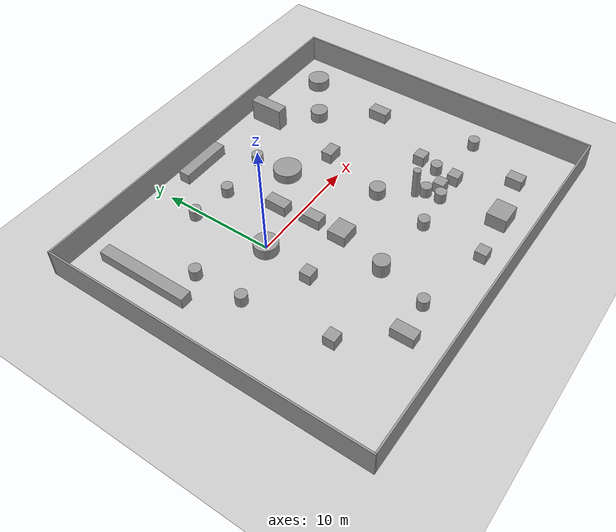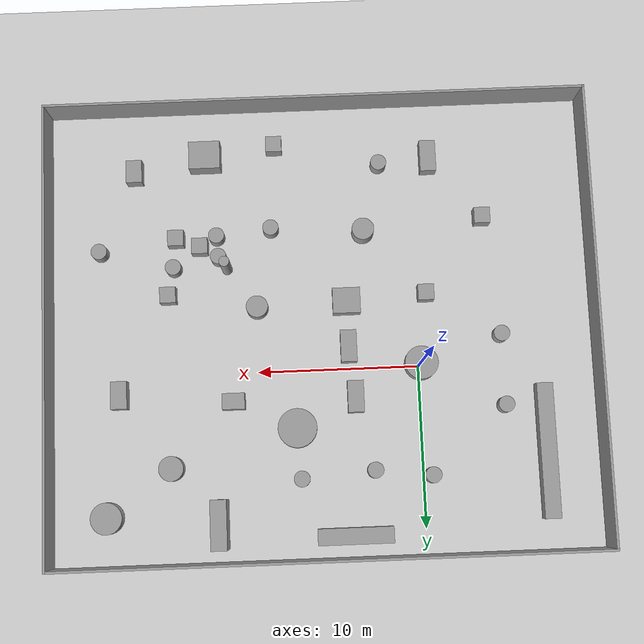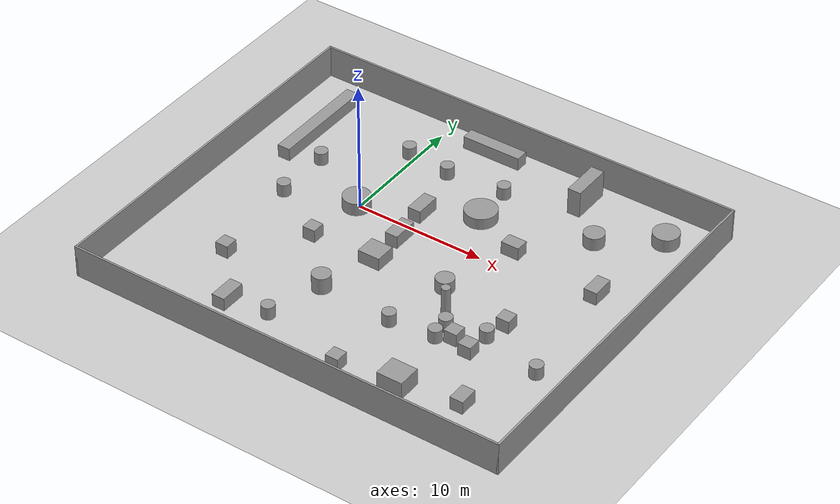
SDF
<sdf version="1.7">
 <world name="default">
  <light name="sun" type="directional">
   <pose>0 0 10 0 -0 0</pose>
   <diffuse>0.8 0.8 0.8 1</diffuse>
   <specular>0.2 0.2 0.2 1</specular>
   <attenuation>
    <range>1000</range>
    <constant>0.9</constant>
    <linear>0.01</linear>
    <quadratic>0.001</quadratic>
   </attenuation>
   <direction>-0.5 0.1 -0.9</direction>
   <spot><inner_angle>0</inner_angle><outer_angle>0</outer_angle><falloff>0</falloff></spot>
  </light>
  <model name="ground_plane">
   <static>1</static>
   <link name="link">
    <collision name="collision">
     <geometry><plane><normal>0 0 1</normal><size>100 100</size></plane></geometry>
     <surface><friction><ode><mu>100</mu><mu2>50</mu2></ode></friction></surface>
    </collision>
    <visual name="visual">
     <cast_shadows>0</cast_shadows>
     <geometry><plane><normal>0 0 1</normal><size>100 100</size></plane></geometry>
     <material>
      <script><uri>file://media/materials/scripts/gazebo.material</uri><name>Gazebo/Grey</name></script>
     </material>
    </visual>
   </link>
  </model>
  <gravity>0 0 -9.8</gravity>
  <magnetic_field>6e-06 2.3e-05 -4.2e-05</magnetic_field>
  <atmosphere type="adiabatic"/>
  <physics type="ode">
   <max_step_size>0.001</max_step_size>
   <real_time_factor>1</real_time_factor>
   <real_time_update_rate>1000</real_time_update_rate>
  </physics>
  <scene><ambient>0.4 0.4 0.4 1</ambient><background>0.7 0.7 0.7 1</background><shadows>1</shadows></scene>
  <spherical_coordinates>
   <surface_model>EARTH_WGS84</surface_model>
   <latitude_deg>0</latitude_deg>
   <longitude_deg>0</longitude_deg>
   <elevation>0</elevation>
   <heading_deg>0</heading_deg>
  </spherical_coordinates>
  <model name="paper_world">
   <pose>5.91262 -2.7055 0 0 -0 0</pose>
   <link name="Wall_10">
    <collision name="Wall_10_Collision">
     <geometry><box><size>34 0.15 2.5</size></box></geometry>
     <pose>0 0 1.25 0 -0 0</pose>
    </collision>
    <visual name="Wall_10_Visual">
     <pose>0 0 1.25 0 -0 0</pose>
     <geometry><box><size>34 0.15 2.5</size></box></geometry>
     <material>
      <script><uri>file://media/materials/scripts/gazebo.material</uri><name>Gazebo/Grey</name></script>
      <ambient>1 1 1 1</ambient>
     </material>
     <meta><layer>0</layer></meta>
    </visual>
    <pose>-0 14.3 0 0 -0 0</pose>
   </link>
   <link name="Wall_2">
    <collision name="Wall_2_Collision">
     <geometry><box><size>28.75 0.15 2.5</size></box></geometry>
     <pose>0 0 1.25 0 -0 0</pose>
    </collision>
    <visual name="Wall_2_Visual">
     <pose>0 0 1.25 0 -0 0</pose>
     <geometry><box><size>28.75 0.15 2.5</size></box></geometry>
     <material>
      <script><uri>file://media/materials/scripts/gazebo.material</uri><name>Gazebo/Grey</name></script>
      <ambient>1 1 1 1</ambient>
     </material>
     <meta><layer>0</layer></meta>
    </visual>
    <pose>-16.925 -0 0 0 -0 -1.5708</pose>
   </link>
   <link name="Wall_3">
    <collision name="Wall_3_Collision">
     <geometry><box><size>34 0.15 2.5</size></box></geometry>
     <pose>0 0 1.25 0 -0 0</pose>
    </collision>
    <visual name="Wall_3_Visual">
     <pose>0 0 1.25 0 -0 0</pose>
     <geometry><box><size>34 0.15 2.5</size></box></geometry>
     <material>
      <script><uri>file://media/materials/scripts/gazebo.material</uri><name>Gazebo/Grey</name></script>
      <ambient>1 1 1 1</ambient>
     </material>
     <meta><layer>0</layer></meta>
    </visual>
    <pose>-0 -14.3 0 0 -0 0</pose>
   </link>
   <link name="Wall_4">
    <collision name="Wall_4_Collision">
     <geometry><box><size>28.75 0.15 2.5</size></box></geometry>
     <pose>0 0 1.25 0 -0 0</pose>
    </collision>
    <visual name="Wall_4_Visual">
     <pose>0 0 1.25 0 -0 0</pose>
     <geometry><box><size>28.75 0.15 2.5</size></box></geometry>
     <material>
      <script><uri>file://media/materials/scripts/gazebo.material</uri><name>Gazebo/Grey</name></script>
      <ambient>1 1 1 1</ambient>
     </material>
     <meta><layer>0</layer></meta>
    </visual>
    <pose>16.925 -0 0 0 -0 1.5708</pose>
   </link>
   <static>1</static>
  </model>
  <model name="test">
   <link name="link_0">
    <inertial>
     <mass>2.35844</mass>
     <inertia><ixx>0.54418</ixx><ixy>0</ixy><ixz>0</ixz><iyy>0.54418</iyy><iyz>0</iyz><izz>0.695287</izz></inertia>
    </inertial>
    <pose>6.8224 9.17542 0 0 -0 0</pose>
    <visual name="visual">
     <geometry><cylinder><radius>0.767864</radius><length>1</length></cylinder></geometry>
     <material>
      <lighting>1</lighting>
      <script><uri>file://media/materials/scripts/gazebo.material</uri><name>Gazebo/Grey</name></script>
      <shader type="pixel"/>
     </material>
    </visual>
    <collision name="collision">
     <geometry><cylinder><radius>0.767864</radius><length>1</length></cylinder></geometry>
     <surface>
      <friction>
       <ode><mu>1</mu><mu2>1</mu2><fdir1>0 0 0</fdir1><slip1>0</slip1><slip2>0</slip2></ode>
       <torsional>
        <coefficient>1</coefficient>
        <patch_radius>0</patch_radius>
        <surface_radius>0</surface_radius>
        <use_patch_radius>1</use_patch_radius>
        <ode><slip>0</slip></ode>
       </torsional>
      </friction>
      <bounce><restitution_coefficient>0</restitution_coefficient><threshold>1e+06</threshold></bounce>
      <contact>
       <collide_without_contact>0</collide_without_contact>
       <collide_without_contact_bitmask>1</collide_without_contact_bitmask>
       <collide_bitmask>1</collide_bitmask>
       <ode>
        <soft_cfm>0</soft_cfm>
        <soft_erp>0.2</soft_erp>
        <kp>1e+13</kp>
        <kd>1</kd>
        <max_vel>0.01</max_vel>
        <min_depth>0</min_depth>
       </ode>
       <bullet>
        <split_impulse>1</split_impulse>
        <split_impulse_penetration_threshold>-0.01</split_impulse_penetration_threshold>
        <soft_cfm>0</soft_cfm>
        <soft_erp>0.2</soft_erp>
        <kp>1e+13</kp>
        <kd>1</kd>
       </bullet>
      </contact>
     </surface>
    </collision>
   </link>
   <link name="link_1">
    <inertial>
     <mass>1.39777</mass>
     <inertia>
      <ixx>0.232962</ixx>
      <ixy>0</ixy>
      <ixz>0</ixz>
      <iyy>0.344058</iyy>
      <iyz>0</iyz>
      <izz>0.344058</izz>
     </inertia>
    </inertial>
    <pose>2.9123 5.19786 0 0 -0 0</pose>
    <visual name="visual">
     <geometry><box><size>1.39777 1 1</size></box></geometry>
     <material>
      <lighting>1</lighting>
      <script><uri>file://media/materials/scripts/gazebo.material</uri><name>Gazebo/Grey</name></script>
      <shader type="pixel"/>
     </material>
    </visual>
    <collision name="collision">
     <geometry><box><size>1.39777 1 1</size></box></geometry>
     <surface>
      <friction>
       <ode><mu>1</mu><mu2>1</mu2><fdir1>0 0 0</fdir1><slip1>0</slip1><slip2>0</slip2></ode>
       <torsional>
        <coefficient>1</coefficient>
        <patch_radius>0</patch_radius>
        <surface_radius>0</surface_radius>
        <use_patch_radius>1</use_patch_radius>
        <ode><slip>0</slip></ode>
       </torsional>
      </friction>
      <bounce><restitution_coefficient>0</restitution_coefficient><threshold>1e+06</threshold></bounce>
      <contact>
       <collide_without_contact>0</collide_without_contact>
       <collide_without_contact_bitmask>1</collide_without_contact_bitmask>
       <collide_bitmask>1</collide_bitmask>
       <ode>
        <soft_cfm>0</soft_cfm>
        <soft_erp>0.2</soft_erp>
        <kp>1e+13</kp>
        <kd>1</kd>
        <max_vel>0.01</max_vel>
        <min_depth>0</min_depth>
       </ode>
       <bullet>
        <split_impulse>1</split_impulse>
        <split_impulse_penetration_threshold>-0.01</split_impulse_penetration_threshold>
        <soft_cfm>0</soft_cfm>
        <soft_erp>0.2</soft_erp>
        <kp>1e+13</kp>
        <kd>1</kd>
       </bullet>
      </contact>
     </surface>
    </collision>
   </link>
   <link name="link_10">
    <inertial>
     <mass>1</mass>
     <inertia>
      <ixx>0.166667</ixx>
      <ixy>0</ixy>
      <ixz>0</ixz>
      <iyy>0.166667</iyy>
      <iyz>0</iyz>
      <izz>0.166667</izz>
     </inertia>
    </inertial>
    <pose>-9.28458 -1.16229 0 0 -0 0</pose>
    <visual name="visual">
     <geometry><box><size>1 1 1</size></box></geometry>
     <material>
      <lighting>1</lighting>
      <script><uri>file://media/materials/scripts/gazebo.material</uri><name>Gazebo/Grey</name></script>
      <shader type="pixel"/>
     </material>
    </visual>
    <collision name="collision">
     <geometry><box><size>1 1 1</size></box></geometry>
     <surface>
      <friction>
       <ode><mu>1</mu><mu2>1</mu2><fdir1>0 0 0</fdir1><slip1>0</slip1><slip2>0</slip2></ode>
       <torsional>
        <coefficient>1</coefficient>
        <patch_radius>0</patch_radius>
        <surface_radius>0</surface_radius>
        <use_patch_radius>1</use_patch_radius>
        <ode><slip>0</slip></ode>
       </torsional>
      </friction>
      <bounce><restitution_coefficient>0</restitution_coefficient><threshold>1e+06</threshold></bounce>
      <contact>
       <collide_without_contact>0</collide_without_contact>
       <collide_without_contact_bitmask>1</collide_without_contact_bitmask>
       <collide_bitmask>1</collide_bitmask>
       <ode>
        <soft_cfm>0</soft_cfm>
        <soft_erp>0.2</soft_erp>
        <kp>1e+13</kp>
        <kd>1</kd>
        <max_vel>0.01</max_vel>
        <min_depth>0</min_depth>
       </ode>
       <bullet>
        <split_impulse>1</split_impulse>
        <split_impulse_penetration_threshold>-0.01</split_impulse_penetration_threshold>
        <soft_cfm>0</soft_cfm>
        <soft_erp>0.2</soft_erp>
        <kp>1e+13</kp>
        <kd>1</kd>
       </bullet>
      </contact>
     </surface>
    </collision>
   </link>
   <link name="link_11">
    <inertial>
     <mass>1</mass>
     <inertia><ixx>0.145833</ixx><ixy>0</ixy><ixz>0</ixz><iyy>0.145833</iyy><iyz>0</iyz><izz>0.125</izz></inertia>
    </inertial>
    <pose>-6.68815 -9.61856 0 0 -0 0</pose>
    <visual name="visual">
     <geometry><cylinder><radius>0.5</radius><length>1</length></cylinder></geometry>
     <material>
      <lighting>1</lighting>
      <script><uri>file://media/materials/scripts/gazebo.material</uri><name>Gazebo/Grey</name></script>
      <shader type="pixel"/>
     </material>
    </visual>
    <collision name="collision">
     <geometry><cylinder><radius>0.5</radius><length>1</length></cylinder></geometry>
     <surface>
      <friction>
       <ode><mu>1</mu><mu2>1</mu2><fdir1>0 0 0</fdir1><slip1>0</slip1><slip2>0</slip2></ode>
       <torsional>
        <coefficient>1</coefficient>
        <patch_radius>0</patch_radius>
        <surface_radius>0</surface_radius>
        <use_patch_radius>1</use_patch_radius>
        <ode><slip>0</slip></ode>
       </torsional>
      </friction>
      <bounce><restitution_coefficient>0</restitution_coefficient><threshold>1e+06</threshold></bounce>
      <contact>
       <collide_without_contact>0</collide_without_contact>
       <collide_without_contact_bitmask>1</collide_without_contact_bitmask>
       <collide_bitmask>1</collide_bitmask>
       <ode>
        <soft_cfm>0</soft_cfm>
        <soft_erp>0.2</soft_erp>
        <kp>1e+13</kp>
        <kd>1</kd>
        <max_vel>0.01</max_vel>
        <min_depth>0</min_depth>
       </ode>
       <bullet>
        <split_impulse>1</split_impulse>
        <split_impulse_penetration_threshold>-0.01</split_impulse_penetration_threshold>
        <soft_cfm>0</soft_cfm>
        <soft_erp>0.2</soft_erp>
        <kp>1e+13</kp>
        <kd>1</kd>
       </bullet>
      </contact>
     </surface>
    </collision>
   </link>
   <link name="link_12">
    <inertial>
     <mass>1</mass>
     <inertia>
      <ixx>0.166667</ixx>
      <ixy>0</ixy>
      <ixz>0</ixz>
      <iyy>0.166667</iyy>
      <iyz>0</iyz>
      <izz>0.166667</izz>
     </inertia>
    </inertial>
    <pose>6.8354 -1.59286 0 0 -0 0</pose>
    <visual name="visual">
     <geometry><box><size>1 1 1</size></box></geometry>
     <material>
      <lighting>1</lighting>
      <script><uri>file://media/materials/scripts/gazebo.material</uri><name>Gazebo/Grey</name></script>
      <shader type="pixel"/>
     </material>
    </visual>
    <collision name="collision">
     <geometry><box><size>1 1 1</size></box></geometry>
     <surface>
      <friction>
       <ode><mu>1</mu><mu2>1</mu2><fdir1>0 0 0</fdir1><slip1>0</slip1><slip2>0</slip2></ode>
       <torsional>
        <coefficient>1</coefficient>
        <patch_radius>0</patch_radius>
        <surface_radius>0</surface_radius>
        <use_patch_radius>1</use_patch_radius>
        <ode><slip>0</slip></ode>
       </torsional>
      </friction>
      <bounce><restitution_coefficient>0</restitution_coefficient><threshold>1e+06</threshold></bounce>
      <contact>
       <collide_without_contact>0</collide_without_contact>
       <collide_without_contact_bitmask>1</collide_without_contact_bitmask>
       <collide_bitmask>1</collide_bitmask>
       <ode>
        <soft_cfm>0</soft_cfm>
        <soft_erp>0.2</soft_erp>
        <kp>1e+13</kp>
        <kd>1</kd>
        <max_vel>0.01</max_vel>
        <min_depth>0</min_depth>
       </ode>
       <bullet>
        <split_impulse>1</split_impulse>
        <split_impulse_penetration_threshold>-0.01</split_impulse_penetration_threshold>
        <soft_cfm>0</soft_cfm>
        <soft_erp>0.2</soft_erp>
        <kp>1e+13</kp>
        <kd>1</kd>
       </bullet>
      </contact>
     </surface>
    </collision>
   </link>
   <link name="link_13">
    <inertial>
     <mass>1</mass>
     <inertia><ixx>0.145833</ixx><ixy>0</ixy><ixz>0</ixz><iyy>0.145833</iyy><iyz>0</iyz><izz>0.125</izz></inertia>
    </inertial>
    <pose>0.279985 -5.64687 0 0 -0 0</pose>
    <visual name="visual">
     <geometry><cylinder><radius>0.5</radius><length>1</length></cylinder></geometry>
     <material>
      <lighting>1</lighting>
      <script><uri>file://media/materials/scripts/gazebo.material</uri><name>Gazebo/Grey</name></script>
      <shader type="pixel"/>
     </material>
    </visual>
    <collision name="collision">
     <geometry><cylinder><radius>0.5</radius><length>1</length></cylinder></geometry>
     <surface>
      <friction>
       <ode><mu>1</mu><mu2>1</mu2><fdir1>0 0 0</fdir1><slip1>0</slip1><slip2>0</slip2></ode>
       <torsional>
        <coefficient>1</coefficient>
        <patch_radius>0</patch_radius>
        <surface_radius>0</surface_radius>
        <use_patch_radius>1</use_patch_radius>
        <ode><slip>0</slip></ode>
       </torsional>
      </friction>
      <bounce><restitution_coefficient>0</restitution_coefficient><threshold>1e+06</threshold></bounce>
      <contact>
       <collide_without_contact>0</collide_without_contact>
       <collide_without_contact_bitmask>1</collide_without_contact_bitmask>
       <collide_bitmask>1</collide_bitmask>
       <ode>
        <soft_cfm>0</soft_cfm>
        <soft_erp>0.2</soft_erp>
        <kp>1e+13</kp>
        <kd>1</kd>
        <max_vel>0.01</max_vel>
        <min_depth>0</min_depth>
       </ode>
       <bullet>
        <split_impulse>1</split_impulse>
        <split_impulse_penetration_threshold>-0.01</split_impulse_penetration_threshold>
        <soft_cfm>0</soft_cfm>
        <soft_erp>0.2</soft_erp>
        <kp>1e+13</kp>
        <kd>1</kd>
       </bullet>
      </contact>
     </surface>
    </collision>
   </link>
   <link name="link_14">
    <inertial>
     <mass>1.71585</mass>
     <inertia>
      <ixx>0.563966</ixx>
      <ixy>0</ixy>
      <ixz>0</ixz>
      <iyy>0.285976</iyy>
      <iyz>0</iyz>
      <izz>0.563966</izz>
     </inertia>
    </inertial>
    <pose>9.96126 4.5598 0 0 -0 0</pose>
    <visual name="visual">
     <geometry><box><size>1 1.71585 1</size></box></geometry>
     <material>
      <lighting>1</lighting>
      <script><uri>file://media/materials/scripts/gazebo.material</uri><name>Gazebo/Grey</name></script>
      <shader type="pixel"/>
     </material>
    </visual>
    <collision name="collision">
     <geometry><box><size>1 1.71585 1</size></box></geometry>
     <surface>
      <friction>
       <ode><mu>1</mu><mu2>1</mu2><fdir1>0 0 0</fdir1><slip1>0</slip1><slip2>0</slip2></ode>
       <torsional>
        <coefficient>1</coefficient>
        <patch_radius>0</patch_radius>
        <surface_radius>0</surface_radius>
        <use_patch_radius>1</use_patch_radius>
        <ode><slip>0</slip></ode>
       </torsional>
      </friction>
      <bounce><restitution_coefficient>0</restitution_coefficient><threshold>1e+06</threshold></bounce>
      <contact>
       <collide_without_contact>0</collide_without_contact>
       <collide_without_contact_bitmask>1</collide_without_contact_bitmask>
       <collide_bitmask>1</collide_bitmask>
       <ode>
        <soft_cfm>0</soft_cfm>
        <soft_erp>0.2</soft_erp>
        <kp>1e+13</kp>
        <kd>1</kd>
        <max_vel>0.01</max_vel>
        <min_depth>0</min_depth>
       </ode>
       <bullet>
        <split_impulse>1</split_impulse>
        <split_impulse_penetration_threshold>-0.01</split_impulse_penetration_threshold>
        <soft_cfm>0</soft_cfm>
        <soft_erp>0.2</soft_erp>
        <kp>1e+13</kp>
        <kd>1</kd>
       </bullet>
      </contact>
     </surface>
    </collision>
   </link>
   <link name="link_15">
    <inertial>
     <mass>1</mass>
     <inertia><ixx>0.145833</ixx><ixy>0</ixy><ixz>0</ixz><iyy>0.145833</iyy><iyz>0</iyz><izz>0.125</izz></inertia>
    </inertial>
    <pose>6.45641 -3.33112 0 0 -0 0</pose>
    <visual name="visual">
     <geometry><cylinder><radius>0.5</radius><length>1</length></cylinder></geometry>
     <material>
      <lighting>1</lighting>
      <script><uri>file://media/materials/scripts/gazebo.material</uri><name>Gazebo/Grey</name></script>
      <shader type="pixel"/>
     </material>
    </visual>
    <collision name="collision">
     <geometry><cylinder><radius>0.5</radius><length>1</length></cylinder></geometry>
     <surface>
      <friction>
       <ode><mu>1</mu><mu2>1</mu2><fdir1>0 0 0</fdir1><slip1>0</slip1><slip2>0</slip2></ode>
       <torsional>
        <coefficient>1</coefficient>
        <patch_radius>0</patch_radius>
        <surface_radius>0</surface_radius>
        <use_patch_radius>1</use_patch_radius>
        <ode><slip>0</slip></ode>
       </torsional>
      </friction>
      <bounce><restitution_coefficient>0</restitution_coefficient><threshold>1e+06</threshold></bounce>
      <contact>
       <collide_without_contact>0</collide_without_contact>
       <collide_without_contact_bitmask>1</collide_without_contact_bitmask>
       <collide_bitmask>1</collide_bitmask>
       <ode>
        <soft_cfm>0</soft_cfm>
        <soft_erp>0.2</soft_erp>
        <kp>1e+13</kp>
        <kd>1</kd>
        <max_vel>0.01</max_vel>
        <min_depth>0</min_depth>
       </ode>
       <bullet>
        <split_impulse>1</split_impulse>
        <split_impulse_penetration_threshold>-0.01</split_impulse_penetration_threshold>
        <soft_cfm>0</soft_cfm>
        <soft_erp>0.2</soft_erp>
        <kp>1e+13</kp>
        <kd>1</kd>
       </bullet>
      </contact>
     </surface>
    </collision>
   </link>
   <link name="link_2">
    <inertial>
     <mass>1</mass>
     <inertia><ixx>0.145833</ixx><ixy>0</ixy><ixz>0</ixz><iyy>0.145833</iyy><iyz>0</iyz><izz>0.125</izz></inertia>
    </inertial>
    <pose>-1.14847 10.0992 0 0 -0 0</pose>
    <visual name="visual">
     <geometry><cylinder><radius>0.5</radius><length>1</length></cylinder></geometry>
     <material>
      <lighting>1</lighting>
      <script><uri>file://media/materials/scripts/gazebo.material</uri><name>Gazebo/Grey</name></script>
      <shader type="pixel"/>
     </material>
    </visual>
    <collision name="collision">
     <geometry><cylinder><radius>0.5</radius><length>1</length></cylinder></geometry>
     <surface>
      <friction>
       <ode><mu>1</mu><mu2>1</mu2><fdir1>0 0 0</fdir1><slip1>0</slip1><slip2>0</slip2></ode>
       <torsional>
        <coefficient>1</coefficient>
        <patch_radius>0</patch_radius>
        <surface_radius>0</surface_radius>
        <use_patch_radius>1</use_patch_radius>
        <ode><slip>0</slip></ode>
       </torsional>
      </friction>
      <bounce><restitution_coefficient>0</restitution_coefficient><threshold>1e+06</threshold></bounce>
      <contact>
       <collide_without_contact>0</collide_without_contact>
       <collide_without_contact_bitmask>1</collide_without_contact_bitmask>
       <collide_bitmask>1</collide_bitmask>
       <ode>
        <soft_cfm>0</soft_cfm>
        <soft_erp>0.2</soft_erp>
        <kp>1e+13</kp>
        <kd>1</kd>
        <max_vel>0.01</max_vel>
        <min_depth>0</min_depth>
       </ode>
       <bullet>
        <split_impulse>1</split_impulse>
        <split_impulse_penetration_threshold>-0.01</split_impulse_penetration_threshold>
        <soft_cfm>0</soft_cfm>
        <soft_erp>0.2</soft_erp>
        <kp>1e+13</kp>
        <kd>1</kd>
       </bullet>
      </contact>
     </surface>
    </collision>
   </link>
   <link name="link_3">
    <inertial>
     <mass>2.75203</mass>
     <inertia>
      <ixx>0.815472</ixx>
      <ixy>0</ixy>
      <ixz>0</ixz>
      <iyy>0.908932</iyy>
      <iyz>0</iyz>
      <izz>1.26573</izz>
     </inertia>
    </inertial>
    <pose>-4.29739 -0.820509 0 0 -0 0</pose>
    <visual name="visual">
     <geometry><box><size>1.72143 1.59869 1</size></box></geometry>
     <material>
      <lighting>1</lighting>
      <script><uri>file://media/materials/scripts/gazebo.material</uri><name>Gazebo/Grey</name></script>
      <shader type="pixel"/>
     </material>
    </visual>
    <collision name="collision">
     <geometry><box><size>1.72143 1.59869 1</size></box></geometry>
     <surface>
      <friction>
       <ode><mu>1</mu><mu2>1</mu2><fdir1>0 0 0</fdir1><slip1>0</slip1><slip2>0</slip2></ode>
       <torsional>
        <coefficient>1</coefficient>
        <patch_radius>0</patch_radius>
        <surface_radius>0</surface_radius>
        <use_patch_radius>1</use_patch_radius>
        <ode><slip>0</slip></ode>
       </torsional>
      </friction>
      <bounce><restitution_coefficient>0</restitution_coefficient><threshold>1e+06</threshold></bounce>
      <contact>
       <collide_without_contact>0</collide_without_contact>
       <collide_without_contact_bitmask>1</collide_without_contact_bitmask>
       <collide_bitmask>1</collide_bitmask>
       <ode>
        <soft_cfm>0</soft_cfm>
        <soft_erp>0.2</soft_erp>
        <kp>1e+13</kp>
        <kd>1</kd>
        <max_vel>0.01</max_vel>
        <min_depth>0</min_depth>
       </ode>
       <bullet>
        <split_impulse>1</split_impulse>
        <split_impulse_penetration_threshold>-0.01</split_impulse_penetration_threshold>
        <soft_cfm>0</soft_cfm>
        <soft_erp>0.2</soft_erp>
        <kp>1e+13</kp>
        <kd>1</kd>
       </bullet>
      </contact>
     </surface>
    </collision>
   </link>
   <link name="link_4">
    <inertial>
     <mass>1</mass>
     <inertia>
      <ixx>0.166667</ixx>
      <ixy>0</ixy>
      <ixz>0</ixz>
      <iyy>0.166667</iyy>
      <iyz>0</iyz>
      <izz>0.166667</izz>
     </inertia>
    </inertial>
    <pose>6.27181 -5.2114 0 0 -0 0</pose>
    <visual name="visual">
     <geometry><box><size>1 1 1</size></box></geometry>
     <material>
      <lighting>1</lighting>
      <script><uri>file://media/materials/scripts/gazebo.material</uri><name>Gazebo/Grey</name></script>
      <shader type="pixel"/>
     </material>
    </visual>
    <collision name="collision">
     <geometry><box><size>1 1 1</size></box></geometry>
     <surface>
      <friction>
       <ode><mu>1</mu><mu2>1</mu2><fdir1>0 0 0</fdir1><slip1>0</slip1><slip2>0</slip2></ode>
       <torsional>
        <coefficient>1</coefficient>
        <patch_radius>0</patch_radius>
        <surface_radius>0</surface_radius>
        <use_patch_radius>1</use_patch_radius>
        <ode><slip>0</slip></ode>
       </torsional>
      </friction>
      <bounce><restitution_coefficient>0</restitution_coefficient><threshold>1e+06</threshold></bounce>
      <contact>
       <collide_without_contact>0</collide_without_contact>
       <collide_without_contact_bitmask>1</collide_without_contact_bitmask>
       <collide_bitmask>1</collide_bitmask>
       <ode>
        <soft_cfm>0</soft_cfm>
        <soft_erp>0.2</soft_erp>
        <kp>1e+13</kp>
        <kd>1</kd>
        <max_vel>0.01</max_vel>
        <min_depth>0</min_depth>
       </ode>
       <bullet>
        <split_impulse>1</split_impulse>
        <split_impulse_penetration_threshold>-0.01</split_impulse_penetration_threshold>
        <soft_cfm>0</soft_cfm>
        <soft_erp>0.2</soft_erp>
        <kp>1e+13</kp>
        <kd>1</kd>
       </bullet>
      </contact>
     </surface>
    </collision>
   </link>
   <link name="link_5">
    <inertial>
     <mass>1.86296</mass>
     <inertia>
      <ixx>0.372161</ixx>
      <ixy>0</ixy>
      <ixz>0</ixz>
      <iyy>0.372161</iyy>
      <iyz>0</iyz>
      <izz>0.433829</izz>
     </inertia>
    </inertial>
    <pose>1.28163 -0.64166 0 0 -0 0</pose>
    <visual name="visual">
     <geometry><cylinder><radius>0.682453</radius><length>1</length></cylinder></geometry>
     <material>
      <lighting>1</lighting>
      <script><uri>file://media/materials/scripts/gazebo.material</uri><name>Gazebo/Grey</name></script>
      <shader type="pixel"/>
     </material>
    </visual>
    <collision name="collision">
     <geometry><cylinder><radius>0.682453</radius><length>1</length></cylinder></geometry>
     <surface>
      <friction>
       <ode><mu>1</mu><mu2>1</mu2><fdir1>0 0 0</fdir1><slip1>0</slip1><slip2>0</slip2></ode>
       <torsional>
        <coefficient>1</coefficient>
        <patch_radius>0</patch_radius>
        <surface_radius>0</surface_radius>
        <use_patch_radius>1</use_patch_radius>
        <ode><slip>0</slip></ode>
       </torsional>
      </friction>
      <bounce><restitution_coefficient>0</restitution_coefficient><threshold>1e+06</threshold></bounce>
      <contact>
       <collide_without_contact>0</collide_without_contact>
       <collide_without_contact_bitmask>1</collide_without_contact_bitmask>
       <collide_bitmask>1</collide_bitmask>
       <ode>
        <soft_cfm>0</soft_cfm>
        <soft_erp>0.2</soft_erp>
        <kp>1e+13</kp>
        <kd>1</kd>
        <max_vel>0.01</max_vel>
        <min_depth>0</min_depth>
       </ode>
       <bullet>
        <split_impulse>1</split_impulse>
        <split_impulse_penetration_threshold>-0.01</split_impulse_penetration_threshold>
        <soft_cfm>0</soft_cfm>
        <soft_erp>0.2</soft_erp>
        <kp>1e+13</kp>
        <kd>1</kd>
       </bullet>
      </contact>
     </surface>
    </collision>
   </link>
   <link name="link_6">
    <inertial>
     <mass>1.96097</mass>
     <inertia>
      <ixx>0.791809</ixx>
      <ixy>0</ixy>
      <ixz>0</ixz>
      <iyy>0.326829</iyy>
      <iyz>0</iyz>
      <izz>0.791809</izz>
     </inertia>
    </inertial>
    <pose>-4.6351 5.17923 0 0 -0 0</pose>
    <visual name="visual">
     <geometry><box><size>1 1.96097 1</size></box></geometry>
     <material>
      <lighting>1</lighting>
      <script><uri>file://media/materials/scripts/gazebo.material</uri><name>Gazebo/Grey</name></script>
      <shader type="pixel"/>
     </material>
    </visual>
    <collision name="collision">
     <geometry><box><size>1 1.96097 1</size></box></geometry>
     <surface>
      <friction>
       <ode><mu>1</mu><mu2>1</mu2><fdir1>0 0 0</fdir1><slip1>0</slip1><slip2>0</slip2></ode>
       <torsional>
        <coefficient>1</coefficient>
        <patch_radius>0</patch_radius>
        <surface_radius>0</surface_radius>
        <use_patch_radius>1</use_patch_radius>
        <ode><slip>0</slip></ode>
       </torsional>
      </friction>
      <bounce><restitution_coefficient>0</restitution_coefficient><threshold>1e+06</threshold></bounce>
      <contact>
       <collide_without_contact>0</collide_without_contact>
       <collide_without_contact_bitmask>1</collide_without_contact_bitmask>
       <collide_bitmask>1</collide_bitmask>
       <ode>
        <soft_cfm>0</soft_cfm>
        <soft_erp>0.2</soft_erp>
        <kp>1e+13</kp>
        <kd>1</kd>
        <max_vel>0.01</max_vel>
        <min_depth>0</min_depth>
       </ode>
       <bullet>
        <split_impulse>1</split_impulse>
        <split_impulse_penetration_threshold>-0.01</split_impulse_penetration_threshold>
        <soft_cfm>0</soft_cfm>
        <soft_erp>0.2</soft_erp>
        <kp>1e+13</kp>
        <kd>1</kd>
       </bullet>
      </contact>
     </surface>
    </collision>
   </link>
   <link name="link_7">
    <inertial>
     <mass>2.94627</mass>
     <inertia>
      <ixx>0.927957</ixx>
      <ixy>0</ixy>
      <ixz>0</ixz>
      <iyy>0.927957</iyy>
      <iyz>0</iyz>
      <izz>0.710438</izz>
     </inertia>
    </inertial>
    <pose>-5.51875 -5.27348 0 0 -0 0</pose>
    <visual name="visual">
     <geometry><cylinder><radius>0.694451</radius><length>1.52733</length></cylinder></geometry>
     <material>
      <lighting>1</lighting>
      <script><uri>file://media/materials/scripts/gazebo.material</uri><name>Gazebo/Grey</name></script>
      <shader type="pixel"/>
     </material>
    </visual>
    <collision name="collision">
     <geometry><cylinder><radius>0.694451</radius><length>1.52733</length></cylinder></geometry>
     <surface>
      <friction>
       <ode><mu>1</mu><mu2>1</mu2><fdir1>0 0 0</fdir1><slip1>0</slip1><slip2>0</slip2></ode>
       <torsional>
        <coefficient>1</coefficient>
        <patch_radius>0</patch_radius>
        <surface_radius>0</surface_radius>
        <use_patch_radius>1</use_patch_radius>
        <ode><slip>0</slip></ode>
       </torsional>
      </friction>
      <bounce><restitution_coefficient>0</restitution_coefficient><threshold>1e+06</threshold></bounce>
      <contact>
       <collide_without_contact>0</collide_without_contact>
       <collide_without_contact_bitmask>1</collide_without_contact_bitmask>
       <collide_bitmask>1</collide_bitmask>
       <ode>
        <soft_cfm>0</soft_cfm>
        <soft_erp>0.2</soft_erp>
        <kp>1e+13</kp>
        <kd>1</kd>
        <max_vel>0.01</max_vel>
        <min_depth>0</min_depth>
       </ode>
       <bullet>
        <split_impulse>1</split_impulse>
        <split_impulse_penetration_threshold>-0.01</split_impulse_penetration_threshold>
        <soft_cfm>0</soft_cfm>
        <soft_erp>0.2</soft_erp>
        <kp>1e+13</kp>
        <kd>1</kd>
       </bullet>
      </contact>
     </surface>
    </collision>
   </link>
   <link name="link_8">
    <inertial>
     <mass>1</mass>
     <inertia>
      <ixx>0.166667</ixx>
      <ixy>0</ixy>
      <ixz>0</ixz>
      <iyy>0.166667</iyy>
      <iyz>0</iyz>
      <izz>0.166667</izz>
     </inertia>
    </inertial>
    <pose>-0.071201 -11.07 0 0 -0 0</pose>
    <visual name="visual">
     <geometry><box><size>1 1 1</size></box></geometry>
     <material>
      <lighting>1</lighting>
      <script><uri>file://media/materials/scripts/gazebo.material</uri><name>Gazebo/Grey</name></script>
      <shader type="pixel"/>
     </material>
    </visual>
    <collision name="collision">
     <geometry><box><size>1 1 1</size></box></geometry>
     <surface>
      <friction>
       <ode><mu>1</mu><mu2>1</mu2><fdir1>0 0 0</fdir1><slip1>0</slip1><slip2>0</slip2></ode>
       <torsional>
        <coefficient>1</coefficient>
        <patch_radius>0</patch_radius>
        <surface_radius>0</surface_radius>
        <use_patch_radius>1</use_patch_radius>
        <ode><slip>0</slip></ode>
       </torsional>
      </friction>
      <bounce><restitution_coefficient>0</restitution_coefficient><threshold>1e+06</threshold></bounce>
      <contact>
       <collide_without_contact>0</collide_without_contact>
       <collide_without_contact_bitmask>1</collide_without_contact_bitmask>
       <collide_bitmask>1</collide_bitmask>
       <ode>
        <soft_cfm>0</soft_cfm>
        <soft_erp>0.2</soft_erp>
        <kp>1e+13</kp>
        <kd>1</kd>
        <max_vel>0.01</max_vel>
        <min_depth>0</min_depth>
       </ode>
       <bullet>
        <split_impulse>1</split_impulse>
        <split_impulse_penetration_threshold>-0.01</split_impulse_penetration_threshold>
        <soft_cfm>0</soft_cfm>
        <soft_erp>0.2</soft_erp>
        <kp>1e+13</kp>
        <kd>1</kd>
       </bullet>
      </contact>
     </surface>
    </collision>
   </link>
   <link name="link_9">
    <inertial>
     <mass>1</mass>
     <inertia><ixx>0.145833</ixx><ixy>0</ixy><ixz>0</ixz><iyy>0.145833</iyy><iyz>0</iyz><izz>0.125</izz></inertia>
    </inertial>
    <pose>-9.1775 10.1571 0 0 -0 0</pose>
    <visual name="visual">
     <geometry><cylinder><radius>0.5</radius><length>1</length></cylinder></geometry>
     <material>
      <lighting>1</lighting>
      <script><uri>file://media/materials/scripts/gazebo.material</uri><name>Gazebo/Grey</name></script>
      <shader type="pixel"/>
     </material>
    </visual>
    <collision name="collision">
     <geometry><cylinder><radius>0.5</radius><length>1</length></cylinder></geometry>
     <surface>
      <friction>
       <ode><mu>1</mu><mu2>1</mu2><fdir1>0 0 0</fdir1><slip1>0</slip1><slip2>0</slip2></ode>
       <torsional>
        <coefficient>1</coefficient>
        <patch_radius>0</patch_radius>
        <surface_radius>0</surface_radius>
        <use_patch_radius>1</use_patch_radius>
        <ode><slip>0</slip></ode>
       </torsional>
      </friction>
      <bounce><restitution_coefficient>0</restitution_coefficient><threshold>1e+06</threshold></bounce>
      <contact>
       <collide_without_contact>0</collide_without_contact>
       <collide_without_contact_bitmask>1</collide_without_contact_bitmask>
       <collide_bitmask>1</collide_bitmask>
       <ode>
        <soft_cfm>0</soft_cfm>
        <soft_erp>0.2</soft_erp>
        <kp>1e+13</kp>
        <kd>1</kd>
        <max_vel>0.01</max_vel>
        <min_depth>0</min_depth>
       </ode>
       <bullet>
        <split_impulse>1</split_impulse>
        <split_impulse_penetration_threshold>-0.01</split_impulse_penetration_threshold>
        <soft_cfm>0</soft_cfm>
        <soft_erp>0.2</soft_erp>
        <kp>1e+13</kp>
        <kd>1</kd>
       </bullet>
      </contact>
     </surface>
    </collision>
   </link>
   <static>1</static>
   <pose>8.6335 -3.39687 0.5 0 -0 0</pose>
  </model>
  <model name="fuza">
   <link name="link_0">
    <inertial>
     <mass>1</mass>
     <inertia><ixx>0.145833</ixx><ixy>0</ixy><ixz>0</ixz><iyy>0.145833</iyy><iyz>0</iyz><izz>0.125</izz></inertia>
    </inertial>
    <pose>-11.9522 5.00292 -0 0 -0 0</pose>
    <visual name="visual">
     <geometry><cylinder><radius>0.5</radius><length>1</length></cylinder></geometry>
     <material>
      <lighting>1</lighting>
      <script><uri>file://media/materials/scripts/gazebo.material</uri><name>Gazebo/Grey</name></script>
      <shader type="pixel"/>
     </material>
    </visual>
    <collision name="collision">
     <geometry><cylinder><radius>0.5</radius><length>1</length></cylinder></geometry>
     <surface>
      <friction>
       <ode><mu>1</mu><mu2>1</mu2><fdir1>0 0 0</fdir1><slip1>0</slip1><slip2>0</slip2></ode>
       <torsional>
        <coefficient>1</coefficient>
        <patch_radius>0</patch_radius>
        <surface_radius>0</surface_radius>
        <use_patch_radius>1</use_patch_radius>
        <ode><slip>0</slip></ode>
       </torsional>
      </friction>
      <bounce><restitution_coefficient>0</restitution_coefficient><threshold>1e+06</threshold></bounce>
      <contact>
       <collide_without_contact>0</collide_without_contact>
       <collide_without_contact_bitmask>1</collide_without_contact_bitmask>
       <collide_bitmask>1</collide_bitmask>
       <ode>
        <soft_cfm>0</soft_cfm>
        <soft_erp>0.2</soft_erp>
        <kp>1e+13</kp>
        <kd>1</kd>
        <max_vel>0.01</max_vel>
        <min_depth>0</min_depth>
       </ode>
       <bullet>
        <split_impulse>1</split_impulse>
        <split_impulse_penetration_threshold>-0.01</split_impulse_penetration_threshold>
        <soft_cfm>0</soft_cfm>
        <soft_erp>0.2</soft_erp>
        <kp>1e+13</kp>
        <kd>1</kd>
       </bullet>
      </contact>
     </surface>
    </collision>
   </link>
   <link name="link_11">
    <inertial>
     <mass>1.98679</mass>
     <inertia>
      <ixx>0.819115</ixx>
      <ixy>0</ixy>
      <ixz>0</ixz>
      <iyy>0.331132</iyy>
      <iyz>0</iyz>
      <izz>0.819115</izz>
     </inertia>
    </inertial>
    <pose>-2.38647 1.012 -0 0 -0 0</pose>
    <visual name="visual">
     <geometry><box><size>1 1.9868 1</size></box></geometry>
     <material>
      <lighting>1</lighting>
      <script><uri>file://media/materials/scripts/gazebo.material</uri><name>Gazebo/Grey</name></script>
      <shader type="pixel"/>
     </material>
    </visual>
    <collision name="collision">
     <geometry><box><size>1 1.9868 1</size></box></geometry>
     <surface>
      <friction>
       <ode><mu>1</mu><mu2>1</mu2><fdir1>0 0 0</fdir1><slip1>0</slip1><slip2>0</slip2></ode>
       <torsional>
        <coefficient>1</coefficient>
        <patch_radius>0</patch_radius>
        <surface_radius>0</surface_radius>
        <use_patch_radius>1</use_patch_radius>
        <ode><slip>0</slip></ode>
       </torsional>
      </friction>
      <bounce><restitution_coefficient>0</restitution_coefficient><threshold>1e+06</threshold></bounce>
      <contact>
       <collide_without_contact>0</collide_without_contact>
       <collide_without_contact_bitmask>1</collide_without_contact_bitmask>
       <collide_bitmask>1</collide_bitmask>
       <ode>
        <soft_cfm>0</soft_cfm>
        <soft_erp>0.2</soft_erp>
        <kp>1e+13</kp>
        <kd>1</kd>
        <max_vel>0.01</max_vel>
        <min_depth>0</min_depth>
       </ode>
       <bullet>
        <split_impulse>1</split_impulse>
        <split_impulse_penetration_threshold>-0.01</split_impulse_penetration_threshold>
        <soft_cfm>0</soft_cfm>
        <soft_erp>0.2</soft_erp>
        <kp>1e+13</kp>
        <kd>1</kd>
       </bullet>
      </contact>
     </surface>
    </collision>
   </link>
   <link name="link_12">
    <inertial>
     <mass>5.11595</mass>
     <inertia><ixx>2.20052</ixx><ixy>0</ixy><ixz>0</ixz><iyy>2.20052</iyy><iyz>0</iyz><izz>3.75336</izz></inertia>
    </inertial>
    <pose>0.962557 5.97068 0 0 -0 0</pose>
    <visual name="visual">
     <geometry><cylinder><radius>1.21133</radius><length>0.871556</length></cylinder></geometry>
     <material>
      <lighting>1</lighting>
      <script><uri>file://media/materials/scripts/gazebo.material</uri><name>Gazebo/Grey</name></script>
      <shader type="pixel"/>
     </material>
    </visual>
    <collision name="collision">
     <geometry><cylinder><radius>1.21133</radius><length>0.871556</length></cylinder></geometry>
     <surface>
      <friction>
       <ode><mu>1</mu><mu2>1</mu2><fdir1>0 0 0</fdir1><slip1>0</slip1><slip2>0</slip2></ode>
       <torsional>
        <coefficient>1</coefficient>
        <patch_radius>0</patch_radius>
        <surface_radius>0</surface_radius>
        <use_patch_radius>1</use_patch_radius>
        <ode><slip>0</slip></ode>
       </torsional>
      </friction>
      <bounce><restitution_coefficient>0</restitution_coefficient><threshold>1e+06</threshold></bounce>
      <contact>
       <collide_without_contact>0</collide_without_contact>
       <collide_without_contact_bitmask>1</collide_without_contact_bitmask>
       <collide_bitmask>1</collide_bitmask>
       <ode>
        <soft_cfm>0</soft_cfm>
        <soft_erp>0.2</soft_erp>
        <kp>1e+13</kp>
        <kd>1</kd>
        <max_vel>0.01</max_vel>
        <min_depth>0</min_depth>
       </ode>
       <bullet>
        <split_impulse>1</split_impulse>
        <split_impulse_penetration_threshold>-0.01</split_impulse_penetration_threshold>
        <soft_cfm>0</soft_cfm>
        <soft_erp>0.2</soft_erp>
        <kp>1e+13</kp>
        <kd>1</kd>
       </bullet>
      </contact>
     </surface>
    </collision>
   </link>
   <link name="link_13">
    <inertial>
     <mass>1.90421</mass>
     <inertia><ixx>3.26258</ixx><ixy>0</ixy><ixz>0</ixz><iyy>3.26258</iyy><iyz>0</iyz><izz>0.100741</izz></inertia>
    </inertial>
    <pose>5.05919 -4.24487 -0 0 -0 0</pose>
    <visual name="visual">
     <geometry><cylinder><radius>0.325283</radius><length>4.4992</length></cylinder></geometry>
     <material>
      <lighting>1</lighting>
      <script><uri>file://media/materials/scripts/gazebo.material</uri><name>Gazebo/Grey</name></script>
      <shader type="pixel"/>
     </material>
    </visual>
    <collision name="collision">
     <geometry><cylinder><radius>0.325283</radius><length>4.4992</length></cylinder></geometry>
     <surface>
      <friction>
       <ode><mu>1</mu><mu2>1</mu2><fdir1>0 0 0</fdir1><slip1>0</slip1><slip2>0</slip2></ode>
       <torsional>
        <coefficient>1</coefficient>
        <patch_radius>0</patch_radius>
        <surface_radius>0</surface_radius>
        <use_patch_radius>1</use_patch_radius>
        <ode><slip>0</slip></ode>
       </torsional>
      </friction>
      <bounce><restitution_coefficient>0</restitution_coefficient><threshold>1e+06</threshold></bounce>
      <contact>
       <collide_without_contact>0</collide_without_contact>
       <collide_without_contact_bitmask>1</collide_without_contact_bitmask>
       <collide_bitmask>1</collide_bitmask>
       <ode>
        <soft_cfm>0</soft_cfm>
        <soft_erp>0.2</soft_erp>
        <kp>1e+13</kp>
        <kd>1</kd>
        <max_vel>0.01</max_vel>
        <min_depth>0</min_depth>
       </ode>
       <bullet>
        <split_impulse>1</split_impulse>
        <split_impulse_penetration_threshold>-0.01</split_impulse_penetration_threshold>
        <soft_cfm>0</soft_cfm>
        <soft_erp>0.2</soft_erp>
        <kp>1e+13</kp>
        <kd>1</kd>
       </bullet>
      </contact>
     </surface>
    </collision>
   </link>
   <link name="link_14">
    <inertial>
     <mass>1.98339</mass>
     <inertia>
      <ixx>0.815475</ixx>
      <ixy>0</ixy>
      <ixz>0</ixz>
      <iyy>0.330564</iyy>
      <iyz>0</iyz>
      <izz>0.815475</izz>
     </inertia>
    </inertial>
    <pose>-7.9015 -10.9556 -0 0 -0 0</pose>
    <visual name="visual">
     <geometry><box><size>1 1.98339 1</size></box></geometry>
     <material>
      <lighting>1</lighting>
      <script><uri>file://media/materials/scripts/gazebo.material</uri><name>Gazebo/Grey</name></script>
      <shader type="pixel"/>
     </material>
    </visual>
    <collision name="collision">
     <geometry><box><size>1 1.98339 1</size></box></geometry>
     <surface>
      <friction>
       <ode><mu>1</mu><mu2>1</mu2><fdir1>0 0 0</fdir1><slip1>0</slip1><slip2>0</slip2></ode>
       <torsional>
        <coefficient>1</coefficient>
        <patch_radius>0</patch_radius>
        <surface_radius>0</surface_radius>
        <use_patch_radius>1</use_patch_radius>
        <ode><slip>0</slip></ode>
       </torsional>
      </friction>
      <bounce><restitution_coefficient>0</restitution_coefficient><threshold>1e+06</threshold></bounce>
      <contact>
       <collide_without_contact>0</collide_without_contact>
       <collide_without_contact_bitmask>1</collide_without_contact_bitmask>
       <collide_bitmask>1</collide_bitmask>
       <ode>
        <soft_cfm>0</soft_cfm>
        <soft_erp>0.2</soft_erp>
        <kp>1e+13</kp>
        <kd>1</kd>
        <max_vel>0.01</max_vel>
        <min_depth>0</min_depth>
       </ode>
       <bullet>
        <split_impulse>1</split_impulse>
        <split_impulse_penetration_threshold>-0.01</split_impulse_penetration_threshold>
        <soft_cfm>0</soft_cfm>
        <soft_erp>0.2</soft_erp>
        <kp>1e+13</kp>
        <kd>1</kd>
       </bullet>
      </contact>
     </surface>
    </collision>
   </link>
   <link name="link_15">
    <inertial>
     <mass>1</mass>
     <inertia><ixx>0.145833</ixx><ixy>0</ixy><ixz>0</ixz><iyy>0.145833</iyy><iyz>0</iyz><izz>0.125</izz></inertia>
    </inertial>
    <pose>5.5608 -4.96359 0 0 -0 0</pose>
    <visual name="visual">
     <geometry><cylinder><radius>0.5</radius><length>1</length></cylinder></geometry>
     <material>
      <lighting>1</lighting>
      <script><uri>file://media/materials/scripts/gazebo.material</uri><name>Gazebo/Grey</name></script>
      <shader type="pixel"/>
     </material>
    </visual>
    <collision name="collision">
     <geometry><cylinder><radius>0.5</radius><length>1</length></cylinder></geometry>
     <surface>
      <friction>
       <ode><mu>1</mu><mu2>1</mu2><fdir1>0 0 0</fdir1><slip1>0</slip1><slip2>0</slip2></ode>
       <torsional>
        <coefficient>1</coefficient>
        <patch_radius>0</patch_radius>
        <surface_radius>0</surface_radius>
        <use_patch_radius>1</use_patch_radius>
        <ode><slip>0</slip></ode>
       </torsional>
      </friction>
      <bounce><restitution_coefficient>0</restitution_coefficient><threshold>1e+06</threshold></bounce>
      <contact>
       <collide_without_contact>0</collide_without_contact>
       <collide_without_contact_bitmask>1</collide_without_contact_bitmask>
       <collide_bitmask>1</collide_bitmask>
       <ode>
        <soft_cfm>0</soft_cfm>
        <soft_erp>0.2</soft_erp>
        <kp>1e+13</kp>
        <kd>1</kd>
        <max_vel>0.01</max_vel>
        <min_depth>0</min_depth>
       </ode>
       <bullet>
        <split_impulse>1</split_impulse>
        <split_impulse_penetration_threshold>-0.01</split_impulse_penetration_threshold>
        <soft_cfm>0</soft_cfm>
        <soft_erp>0.2</soft_erp>
        <kp>1e+13</kp>
        <kd>1</kd>
       </bullet>
      </contact>
     </surface>
    </collision>
   </link>
   <link name="link_16">
    <inertial>
     <mass>1</mass>
     <inertia><ixx>0.145833</ixx><ixy>0</ixy><ixz>0</ixz><iyy>0.145833</iyy><iyz>0</iyz><izz>0.125</izz></inertia>
    </inertial>
    <pose>5.64099 -6.28555 -0 0 -0 0</pose>
    <visual name="visual">
     <geometry><cylinder><radius>0.5</radius><length>1</length></cylinder></geometry>
     <material>
      <lighting>1</lighting>
      <script><uri>file://media/materials/scripts/gazebo.material</uri><name>Gazebo/Grey</name></script>
      <shader type="pixel"/>
     </material>
    </visual>
    <collision name="collision">
     <geometry><cylinder><radius>0.5</radius><length>1</length></cylinder></geometry>
     <surface>
      <friction>
       <ode><mu>1</mu><mu2>1</mu2><fdir1>0 0 0</fdir1><slip1>0</slip1><slip2>0</slip2></ode>
       <torsional>
        <coefficient>1</coefficient>
        <patch_radius>0</patch_radius>
        <surface_radius>0</surface_radius>
        <use_patch_radius>1</use_patch_radius>
        <ode><slip>0</slip></ode>
       </torsional>
      </friction>
      <bounce><restitution_coefficient>0</restitution_coefficient><threshold>1e+06</threshold></bounce>
      <contact>
       <collide_without_contact>0</collide_without_contact>
       <collide_without_contact_bitmask>1</collide_without_contact_bitmask>
       <collide_bitmask>1</collide_bitmask>
       <ode>
        <soft_cfm>0</soft_cfm>
        <soft_erp>0.2</soft_erp>
        <kp>1e+13</kp>
        <kd>1</kd>
        <max_vel>0.01</max_vel>
        <min_depth>0</min_depth>
       </ode>
       <bullet>
        <split_impulse>1</split_impulse>
        <split_impulse_penetration_threshold>-0.01</split_impulse_penetration_threshold>
        <soft_cfm>0</soft_cfm>
        <soft_erp>0.2</soft_erp>
        <kp>1e+13</kp>
        <kd>1</kd>
       </bullet>
      </contact>
     </surface>
    </collision>
   </link>
   <link name="link_18">
    <inertial>
     <mass>1</mass>
     <inertia>
      <ixx>0.166667</ixx>
      <ixy>0</ixy>
      <ixz>0</ixz>
      <iyy>0.166667</iyy>
      <iyz>0</iyz>
      <izz>0.166667</izz>
     </inertia>
    </inertial>
    <pose>6.71491 -5.66967 0 0 -0 0</pose>
    <visual name="visual">
     <geometry><box><size>1 1 1</size></box></geometry>
     <material>
      <lighting>1</lighting>
      <script><uri>file://media/materials/scripts/gazebo.material</uri><name>Gazebo/Grey</name></script>
      <shader type="pixel"/>
     </material>
    </visual>
    <collision name="collision">
     <geometry><box><size>1 1 1</size></box></geometry>
     <surface>
      <friction>
       <ode><mu>1</mu><mu2>1</mu2><fdir1>0 0 0</fdir1><slip1>0</slip1><slip2>0</slip2></ode>
       <torsional>
        <coefficient>1</coefficient>
        <patch_radius>0</patch_radius>
        <surface_radius>0</surface_radius>
        <use_patch_radius>1</use_patch_radius>
        <ode><slip>0</slip></ode>
       </torsional>
      </friction>
      <bounce><restitution_coefficient>0</restitution_coefficient><threshold>1e+06</threshold></bounce>
      <contact>
       <collide_without_contact>0</collide_without_contact>
       <collide_without_contact_bitmask>1</collide_without_contact_bitmask>
       <collide_bitmask>1</collide_bitmask>
       <ode>
        <soft_cfm>0</soft_cfm>
        <soft_erp>0.2</soft_erp>
        <kp>1e+13</kp>
        <kd>1</kd>
        <max_vel>0.01</max_vel>
        <min_depth>0</min_depth>
       </ode>
       <bullet>
        <split_impulse>1</split_impulse>
        <split_impulse_penetration_threshold>-0.01</split_impulse_penetration_threshold>
        <soft_cfm>0</soft_cfm>
        <soft_erp>0.2</soft_erp>
        <kp>1e+13</kp>
        <kd>1</kd>
       </bullet>
      </contact>
     </surface>
    </collision>
   </link>
   <link name="link_19">
    <inertial>
     <mass>8.27389</mass>
     <inertia><ixx>47.89</ixx><ixy>0</ixy><ixz>0</ixz><iyy>1.37898</iyy><iyz>0</iyz><izz>47.89</izz></inertia>
    </inertial>
    <pose>-14.3414 7.91214 0 0 -0 0</pose>
    <visual name="visual">
     <geometry><box><size>1 8.27388 1</size></box></geometry>
     <material>
      <lighting>1</lighting>
      <script><uri>file://media/materials/scripts/gazebo.material</uri><name>Gazebo/Grey</name></script>
      <shader type="pixel"/>
     </material>
    </visual>
    <collision name="collision">
     <geometry><box><size>1 8.27388 1</size></box></geometry>
     <surface>
      <friction>
       <ode><mu>1</mu><mu2>1</mu2><fdir1>0 0 0</fdir1><slip1>0</slip1><slip2>0</slip2></ode>
       <torsional>
        <coefficient>1</coefficient>
        <patch_radius>0</patch_radius>
        <surface_radius>0</surface_radius>
        <use_patch_radius>1</use_patch_radius>
        <ode><slip>0</slip></ode>
       </torsional>
      </friction>
      <bounce><restitution_coefficient>0</restitution_coefficient><threshold>1e+06</threshold></bounce>
      <contact>
       <collide_without_contact>0</collide_without_contact>
       <collide_without_contact_bitmask>1</collide_without_contact_bitmask>
       <collide_bitmask>1</collide_bitmask>
       <ode>
        <soft_cfm>0</soft_cfm>
        <soft_erp>0.2</soft_erp>
        <kp>1e+13</kp>
        <kd>1</kd>
        <max_vel>0.01</max_vel>
        <min_depth>0</min_depth>
       </ode>
       <bullet>
        <split_impulse>1</split_impulse>
        <split_impulse_penetration_threshold>-0.01</split_impulse_penetration_threshold>
        <soft_cfm>0</soft_cfm>
        <soft_erp>0.2</soft_erp>
        <kp>1e+13</kp>
        <kd>1</kd>
       </bullet>
      </contact>
     </surface>
    </collision>
   </link>
   <link name="link_2">
    <inertial>
     <mass>1</mass>
     <inertia>
      <ixx>0.166667</ixx>
      <ixy>0</ixy>
      <ixz>0</ixz>
      <iyy>0.166667</iyy>
      <iyz>0</iyz>
      <izz>0.166667</izz>
     </inertia>
    </inertial>
    <pose>-11.1282 -6.95628 -0 0 -0 0</pose>
    <visual name="visual">
     <geometry><box><size>1 1 1</size></box></geometry>
     <material>
      <lighting>1</lighting>
      <script><uri>file://media/materials/scripts/gazebo.material</uri><name>Gazebo/Grey</name></script>
      <shader type="pixel"/>
     </material>
    </visual>
    <collision name="collision">
     <geometry><box><size>1 1 1</size></box></geometry>
     <surface>
      <friction>
       <ode><mu>1</mu><mu2>1</mu2><fdir1>0 0 0</fdir1><slip1>0</slip1><slip2>0</slip2></ode>
       <torsional>
        <coefficient>1</coefficient>
        <patch_radius>0</patch_radius>
        <surface_radius>0</surface_radius>
        <use_patch_radius>1</use_patch_radius>
        <ode><slip>0</slip></ode>
       </torsional>
      </friction>
      <bounce><restitution_coefficient>0</restitution_coefficient><threshold>1e+06</threshold></bounce>
      <contact>
       <collide_without_contact>0</collide_without_contact>
       <collide_without_contact_bitmask>1</collide_without_contact_bitmask>
       <collide_bitmask>1</collide_bitmask>
       <ode>
        <soft_cfm>0</soft_cfm>
        <soft_erp>0.2</soft_erp>
        <kp>1e+13</kp>
        <kd>1</kd>
        <max_vel>0.01</max_vel>
        <min_depth>0</min_depth>
       </ode>
       <bullet>
        <split_impulse>1</split_impulse>
        <split_impulse_penetration_threshold>-0.01</split_impulse_penetration_threshold>
        <soft_cfm>0</soft_cfm>
        <soft_erp>0.2</soft_erp>
        <kp>1e+13</kp>
        <kd>1</kd>
       </bullet>
      </contact>
     </surface>
    </collision>
   </link>
   <link name="link_20">
    <inertial>
     <mass>4.63111</mass>
     <inertia><ixx>0.771852</ixx><ixy>0</ixy><ixz>0</ixz><iyy>8.66298</iyy><iyz>0</iyz><izz>8.66298</izz></inertia>
    </inertial>
    <pose>-2.34904 12.6192 0 0 -0 0</pose>
    <visual name="visual">
     <geometry><box><size>4.63112 1 1</size></box></geometry>
     <material>
      <lighting>1</lighting>
      <script><uri>file://media/materials/scripts/gazebo.material</uri><name>Gazebo/Grey</name></script>
      <shader type="pixel"/>
     </material>
    </visual>
    <collision name="collision">
     <geometry><box><size>4.63112 1 1</size></box></geometry>
     <surface>
      <friction>
       <ode><mu>1</mu><mu2>1</mu2><fdir1>0 0 0</fdir1><slip1>0</slip1><slip2>0</slip2></ode>
       <torsional>
        <coefficient>1</coefficient>
        <patch_radius>0</patch_radius>
        <surface_radius>0</surface_radius>
        <use_patch_radius>1</use_patch_radius>
        <ode><slip>0</slip></ode>
       </torsional>
      </friction>
      <bounce><restitution_coefficient>0</restitution_coefficient><threshold>1e+06</threshold></bounce>
      <contact>
       <collide_without_contact>0</collide_without_contact>
       <collide_without_contact_bitmask>1</collide_without_contact_bitmask>
       <collide_bitmask>1</collide_bitmask>
       <ode>
        <soft_cfm>0</soft_cfm>
        <soft_erp>0.2</soft_erp>
        <kp>1e+13</kp>
        <kd>1</kd>
        <max_vel>0.01</max_vel>
        <min_depth>0</min_depth>
       </ode>
       <bullet>
        <split_impulse>1</split_impulse>
        <split_impulse_penetration_threshold>-0.01</split_impulse_penetration_threshold>
        <soft_cfm>0</soft_cfm>
        <soft_erp>0.2</soft_erp>
        <kp>1e+13</kp>
        <kd>1</kd>
       </bullet>
      </contact>
     </surface>
    </collision>
   </link>
   <link name="link_21">
    <inertial>
     <mass>1</mass>
     <inertia><ixx>0.145833</ixx><ixy>0</ixy><ixz>0</ixz><iyy>0.145833</iyy><iyz>0</iyz><izz>0.125</izz></inertia>
    </inertial>
    <pose>-11.9174 0.594151 0 0 -0 0</pose>
    <visual name="visual">
     <geometry><cylinder><radius>0.5</radius><length>1</length></cylinder></geometry>
     <material>
      <lighting>1</lighting>
      <script><uri>file://media/materials/scripts/gazebo.material</uri><name>Gazebo/Grey</name></script>
      <shader type="pixel"/>
     </material>
    </visual>
    <collision name="collision">
     <geometry><cylinder><radius>0.5</radius><length>1</length></cylinder></geometry>
     <surface>
      <friction>
       <ode><mu>1</mu><mu2>1</mu2><fdir1>0 0 0</fdir1><slip1>0</slip1><slip2>0</slip2></ode>
       <torsional>
        <coefficient>1</coefficient>
        <patch_radius>0</patch_radius>
        <surface_radius>0</surface_radius>
        <use_patch_radius>1</use_patch_radius>
        <ode><slip>0</slip></ode>
       </torsional>
      </friction>
      <bounce><restitution_coefficient>0</restitution_coefficient><threshold>1e+06</threshold></bounce>
      <contact>
       <collide_without_contact>0</collide_without_contact>
       <collide_without_contact_bitmask>1</collide_without_contact_bitmask>
       <collide_bitmask>1</collide_bitmask>
       <ode>
        <soft_cfm>0</soft_cfm>
        <soft_erp>0.2</soft_erp>
        <kp>1e+13</kp>
        <kd>1</kd>
        <max_vel>0.01</max_vel>
        <min_depth>0</min_depth>
       </ode>
       <bullet>
        <split_impulse>1</split_impulse>
        <split_impulse_penetration_threshold>-0.01</split_impulse_penetration_threshold>
        <soft_cfm>0</soft_cfm>
        <soft_erp>0.2</soft_erp>
        <kp>1e+13</kp>
        <kd>1</kd>
       </bullet>
      </contact>
     </surface>
    </collision>
   </link>
   <link name="link_22">
    <inertial>
     <mass>4.29206</mass>
     <inertia><ixx>1.50903</ixx><ixy>0</ixy><ixz>0</ixz><iyy>1.50903</iyy><iyz>0</iyz><izz>2.30273</izz></inertia>
    </inertial>
    <pose>-6.85437 2.23218 -0 0 -0 0</pose>
    <visual name="visual">
     <geometry><cylinder><radius>1.03587</radius><length>1</length></cylinder></geometry>
     <material>
      <lighting>1</lighting>
      <script><uri>file://media/materials/scripts/gazebo.material</uri><name>Gazebo/Grey</name></script>
      <shader type="pixel"/>
     </material>
    </visual>
    <collision name="collision">
     <geometry><cylinder><radius>1.03587</radius><length>1</length></cylinder></geometry>
     <surface>
      <friction>
       <ode><mu>1</mu><mu2>1</mu2><fdir1>0 0 0</fdir1><slip1>0</slip1><slip2>0</slip2></ode>
       <torsional>
        <coefficient>1</coefficient>
        <patch_radius>0</patch_radius>
        <surface_radius>0</surface_radius>
        <use_patch_radius>1</use_patch_radius>
        <ode><slip>0</slip></ode>
       </torsional>
      </friction>
      <bounce><restitution_coefficient>0</restitution_coefficient><threshold>1e+06</threshold></bounce>
      <contact>
       <collide_without_contact>0</collide_without_contact>
       <collide_without_contact_bitmask>1</collide_without_contact_bitmask>
       <collide_bitmask>1</collide_bitmask>
       <ode>
        <soft_cfm>0</soft_cfm>
        <soft_erp>0.2</soft_erp>
        <kp>1e+13</kp>
        <kd>1</kd>
        <max_vel>0.01</max_vel>
        <min_depth>0</min_depth>
       </ode>
       <bullet>
        <split_impulse>1</split_impulse>
        <split_impulse_penetration_threshold>-0.01</split_impulse_penetration_threshold>
        <soft_cfm>0</soft_cfm>
        <soft_erp>0.2</soft_erp>
        <kp>1e+13</kp>
        <kd>1</kd>
       </bullet>
      </contact>
     </surface>
    </collision>
   </link>
   <link name="link_3">
    <inertial>
     <mass>3.79853</mass>
     <inertia><ixx>1.21835</ixx><ixy>0</ixy><ixz>0</ixz><iyy>1.21835</iyy><iyz>0</iyz><izz>1.80362</izz></inertia>
    </inertial>
    <pose>12.7402 11.0073 0 0 -0 0</pose>
    <visual name="visual">
     <geometry><cylinder><radius>0.974495</radius><length>1</length></cylinder></geometry>
     <material>
      <lighting>1</lighting>
      <script><uri>file://media/materials/scripts/gazebo.material</uri><name>Gazebo/Grey</name></script>
      <shader type="pixel"/>
     </material>
    </visual>
    <collision name="collision">
     <geometry><cylinder><radius>0.974495</radius><length>1</length></cylinder></geometry>
     <surface>
      <friction>
       <ode><mu>1</mu><mu2>1</mu2><fdir1>0 0 0</fdir1><slip1>0</slip1><slip2>0</slip2></ode>
       <torsional>
        <coefficient>1</coefficient>
        <patch_radius>0</patch_radius>
        <surface_radius>0</surface_radius>
        <use_patch_radius>1</use_patch_radius>
        <ode><slip>0</slip></ode>
       </torsional>
      </friction>
      <bounce><restitution_coefficient>0</restitution_coefficient><threshold>1e+06</threshold></bounce>
      <contact>
       <collide_without_contact>0</collide_without_contact>
       <collide_without_contact_bitmask>1</collide_without_contact_bitmask>
       <collide_bitmask>1</collide_bitmask>
       <ode>
        <soft_cfm>0</soft_cfm>
        <soft_erp>0.2</soft_erp>
        <kp>1e+13</kp>
        <kd>1</kd>
        <max_vel>0.01</max_vel>
        <min_depth>0</min_depth>
       </ode>
       <bullet>
        <split_impulse>1</split_impulse>
        <split_impulse_penetration_threshold>-0.01</split_impulse_penetration_threshold>
        <soft_cfm>0</soft_cfm>
        <soft_erp>0.2</soft_erp>
        <kp>1e+13</kp>
        <kd>1</kd>
       </bullet>
      </contact>
     </surface>
    </collision>
   </link>
   <link name="link_5">
    <inertial>
     <mass>1.43534</mass>
     <inertia>
      <ixx>0.366036</ixx>
      <ixy>0</ixy>
      <ixz>0</ixz>
      <iyy>0.239224</iyy>
      <iyz>0</iyz>
      <izz>0.366036</izz>
     </inertia>
    </inertial>
    <pose>10.7534 -10.6365 -0 0 -0 0</pose>
    <visual name="visual">
     <geometry><box><size>1 1.43534 1</size></box></geometry>
     <material>
      <lighting>1</lighting>
      <script><uri>file://media/materials/scripts/gazebo.material</uri><name>Gazebo/Grey</name></script>
      <shader type="pixel"/>
     </material>
    </visual>
    <collision name="collision">
     <geometry><box><size>1 1.43534 1</size></box></geometry>
     <surface>
      <friction>
       <ode><mu>1</mu><mu2>1</mu2><fdir1>0 0 0</fdir1><slip1>0</slip1><slip2>0</slip2></ode>
       <torsional>
        <coefficient>1</coefficient>
        <patch_radius>0</patch_radius>
        <surface_radius>0</surface_radius>
        <use_patch_radius>1</use_patch_radius>
        <ode><slip>0</slip></ode>
       </torsional>
      </friction>
      <bounce><restitution_coefficient>0</restitution_coefficient><threshold>1e+06</threshold></bounce>
      <contact>
       <collide_without_contact>0</collide_without_contact>
       <collide_without_contact_bitmask>1</collide_without_contact_bitmask>
       <collide_bitmask>1</collide_bitmask>
       <ode>
        <soft_cfm>0</soft_cfm>
        <soft_erp>0.2</soft_erp>
        <kp>1e+13</kp>
        <kd>1</kd>
        <max_vel>0.01</max_vel>
        <min_depth>0</min_depth>
       </ode>
       <bullet>
        <split_impulse>1</split_impulse>
        <split_impulse_penetration_threshold>-0.01</split_impulse_penetration_threshold>
        <soft_cfm>0</soft_cfm>
        <soft_erp>0.2</soft_erp>
        <kp>1e+13</kp>
        <kd>1</kd>
       </bullet>
      </contact>
     </surface>
    </collision>
   </link>
   <link name="link_6">
    <inertial>
     <mass>1</mass>
     <inertia><ixx>0.145833</ixx><ixy>0</ixy><ixz>0</ixz><iyy>0.145833</iyy><iyz>0</iyz><izz>0.125</izz></inertia>
    </inertial>
    <pose>13.0175 -5.51774 -0 0 -0 0</pose>
    <visual name="visual">
     <geometry><cylinder><radius>0.5</radius><length>1</length></cylinder></geometry>
     <material>
      <lighting>1</lighting>
      <script><uri>file://media/materials/scripts/gazebo.material</uri><name>Gazebo/Grey</name></script>
      <shader type="pixel"/>
     </material>
    </visual>
    <collision name="collision">
     <geometry><cylinder><radius>0.5</radius><length>1</length></cylinder></geometry>
     <surface>
      <friction>
       <ode><mu>1</mu><mu2>1</mu2><fdir1>0 0 0</fdir1><slip1>0</slip1><slip2>0</slip2></ode>
       <torsional>
        <coefficient>1</coefficient>
        <patch_radius>0</patch_radius>
        <surface_radius>0</surface_radius>
        <use_patch_radius>1</use_patch_radius>
        <ode><slip>0</slip></ode>
       </torsional>
      </friction>
      <bounce><restitution_coefficient>0</restitution_coefficient><threshold>1e+06</threshold></bounce>
      <contact>
       <collide_without_contact>0</collide_without_contact>
       <collide_without_contact_bitmask>1</collide_without_contact_bitmask>
       <collide_bitmask>1</collide_bitmask>
       <ode>
        <soft_cfm>0</soft_cfm>
        <soft_erp>0.2</soft_erp>
        <kp>1e+13</kp>
        <kd>1</kd>
        <max_vel>0.01</max_vel>
        <min_depth>0</min_depth>
       </ode>
       <bullet>
        <split_impulse>1</split_impulse>
        <split_impulse_penetration_threshold>-0.01</split_impulse_penetration_threshold>
        <soft_cfm>0</soft_cfm>
        <soft_erp>0.2</soft_erp>
        <kp>1e+13</kp>
        <kd>1</kd>
       </bullet>
      </contact>
     </surface>
    </collision>
   </link>
   <link name="link_7">
    <inertial>
     <mass>5.30995</mass>
     <inertia><ixx>2.41036</ixx><ixy>0</ixy><ixz>0</ixz><iyy>2.75199</iyy><iyz>0</iyz><izz>3.08949</izz></inertia>
    </inertial>
    <pose>6.24874 -11.4651 0 0 -0 0</pose>
    <visual name="visual">
     <geometry><box><size>1.96901 1.76209 1.53044</size></box></geometry>
     <material>
      <lighting>1</lighting>
      <script><uri>file://media/materials/scripts/gazebo.material</uri><name>Gazebo/Grey</name></script>
      <shader type="pixel"/>
     </material>
    </visual>
    <collision name="collision">
     <geometry><box><size>1.96901 1.76209 1.53044</size></box></geometry>
     <surface>
      <friction>
       <ode><mu>1</mu><mu2>1</mu2><fdir1>0 0 0</fdir1><slip1>0</slip1><slip2>0</slip2></ode>
       <torsional>
        <coefficient>1</coefficient>
        <patch_radius>0</patch_radius>
        <surface_radius>0</surface_radius>
        <use_patch_radius>1</use_patch_radius>
        <ode><slip>0</slip></ode>
       </torsional>
      </friction>
      <bounce><restitution_coefficient>0</restitution_coefficient><threshold>1e+06</threshold></bounce>
      <contact>
       <collide_without_contact>0</collide_without_contact>
       <collide_without_contact_bitmask>1</collide_without_contact_bitmask>
       <collide_bitmask>1</collide_bitmask>
       <ode>
        <soft_cfm>0</soft_cfm>
        <soft_erp>0.2</soft_erp>
        <kp>1e+13</kp>
        <kd>1</kd>
        <max_vel>0.01</max_vel>
        <min_depth>0</min_depth>
       </ode>
       <bullet>
        <split_impulse>1</split_impulse>
        <split_impulse_penetration_threshold>-0.01</split_impulse_penetration_threshold>
        <soft_cfm>0</soft_cfm>
        <soft_erp>0.2</soft_erp>
        <kp>1e+13</kp>
        <kd>1</kd>
       </bullet>
      </contact>
     </surface>
    </collision>
   </link>
   <link name="link_8">
    <inertial>
     <mass>1</mass>
     <inertia><ixx>0.145833</ixx><ixy>0</ixy><ixz>0</ixz><iyy>0.145833</iyy><iyz>0</iyz><izz>0.125</izz></inertia>
    </inertial>
    <pose>-3.72384 8.71536 0 0 -0 0</pose>
    <visual name="visual">
     <geometry><cylinder><radius>0.5</radius><length>1</length></cylinder></geometry>
     <material>
      <lighting>1</lighting>
      <script><uri>file://media/materials/scripts/gazebo.material</uri><name>Gazebo/Grey</name></script>
      <shader type="pixel"/>
     </material>
    </visual>
    <collision name="collision">
     <geometry><cylinder><radius>0.5</radius><length>1</length></cylinder></geometry>
     <surface>
      <friction>
       <ode><mu>1</mu><mu2>1</mu2><fdir1>0 0 0</fdir1><slip1>0</slip1><slip2>0</slip2></ode>
       <torsional>
        <coefficient>1</coefficient>
        <patch_radius>0</patch_radius>
        <surface_radius>0</surface_radius>
        <use_patch_radius>1</use_patch_radius>
        <ode><slip>0</slip></ode>
       </torsional>
      </friction>
      <bounce><restitution_coefficient>0</restitution_coefficient><threshold>1e+06</threshold></bounce>
      <contact>
       <collide_without_contact>0</collide_without_contact>
       <collide_without_contact_bitmask>1</collide_without_contact_bitmask>
       <collide_bitmask>1</collide_bitmask>
       <ode>
        <soft_cfm>0</soft_cfm>
        <soft_erp>0.2</soft_erp>
        <kp>1e+13</kp>
        <kd>1</kd>
        <max_vel>0.01</max_vel>
        <min_depth>0</min_depth>
       </ode>
       <bullet>
        <split_impulse>1</split_impulse>
        <split_impulse_penetration_threshold>-0.01</split_impulse_penetration_threshold>
        <soft_cfm>0</soft_cfm>
        <soft_erp>0.2</soft_erp>
        <kp>1e+13</kp>
        <kd>1</kd>
       </bullet>
      </contact>
     </surface>
    </collision>
   </link>
   <link name="link_9">
    <inertial>
     <mass>9.26827</mass>
     <inertia><ixx>14.3177</ixx><ixy>0</ixy><ixz>0</ixz><iyy>8.0152</iyy><iyz>0</iyz><izz>7.84724</izz></inertia>
    </inertial>
    <pose>5.85632 11.6291 -0 0 -0 0</pose>
    <visual name="visual">
     <geometry><box><size>1 3.02657 3.06229</size></box></geometry>
     <material>
      <lighting>1</lighting>
      <script><uri>file://media/materials/scripts/gazebo.material</uri><name>Gazebo/Grey</name></script>
      <shader type="pixel"/>
     </material>
    </visual>
    <collision name="collision">
     <geometry><box><size>1 3.02657 3.06229</size></box></geometry>
     <surface>
      <friction>
       <ode><mu>1</mu><mu2>1</mu2><fdir1>0 0 0</fdir1><slip1>0</slip1><slip2>0</slip2></ode>
       <torsional>
        <coefficient>1</coefficient>
        <patch_radius>0</patch_radius>
        <surface_radius>0</surface_radius>
        <use_patch_radius>1</use_patch_radius>
        <ode><slip>0</slip></ode>
       </torsional>
      </friction>
      <bounce><restitution_coefficient>0</restitution_coefficient><threshold>1e+06</threshold></bounce>
      <contact>
       <collide_without_contact>0</collide_without_contact>
       <collide_without_contact_bitmask>1</collide_without_contact_bitmask>
       <collide_bitmask>1</collide_bitmask>
       <ode>
        <soft_cfm>0</soft_cfm>
        <soft_erp>0.2</soft_erp>
        <kp>1e+13</kp>
        <kd>1</kd>
        <max_vel>0.01</max_vel>
        <min_depth>0</min_depth>
       </ode>
       <bullet>
        <split_impulse>1</split_impulse>
        <split_impulse_penetration_threshold>-0.01</split_impulse_penetration_threshold>
        <soft_cfm>0</soft_cfm>
        <soft_erp>0.2</soft_erp>
        <kp>1e+13</kp>
        <kd>1</kd>
       </bullet>
      </contact>
     </surface>
    </collision>
   </link>
   <static>1</static>
   <pose>6.69742 -2.37714 0.500031 -2e-06 -2e-06 0</pose>
  </model>
 </world>
</sdf>
